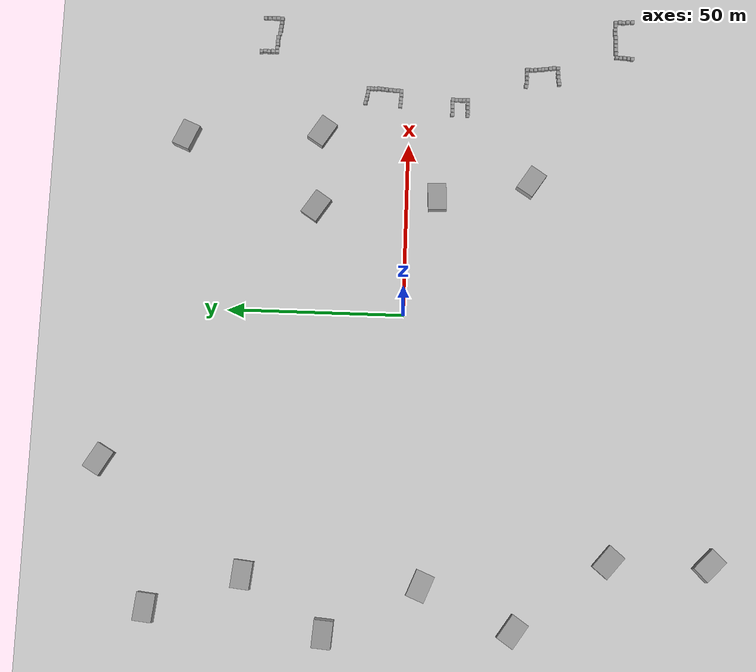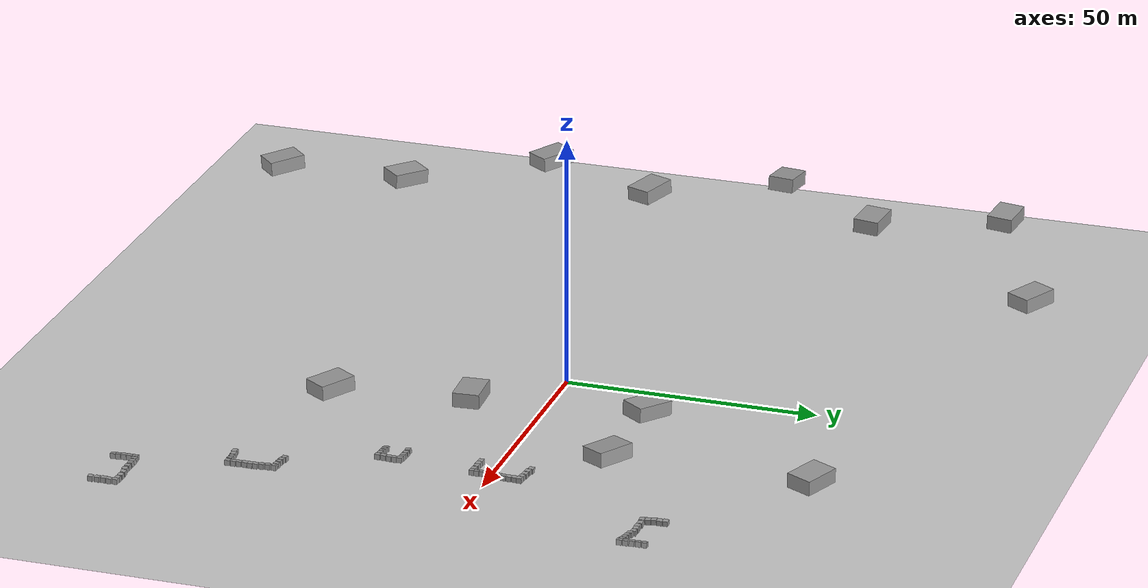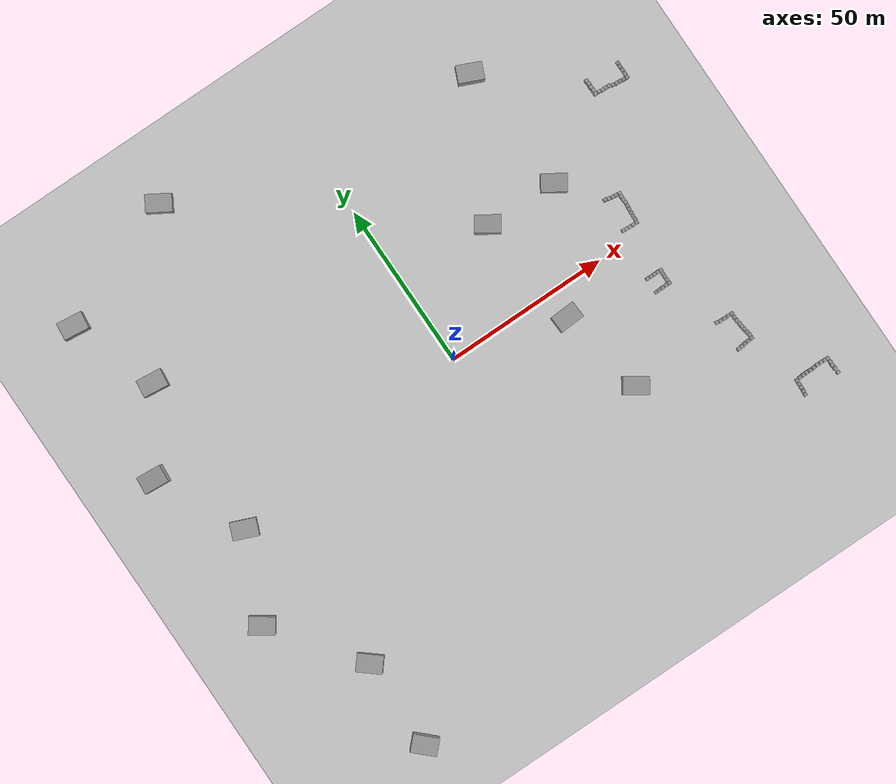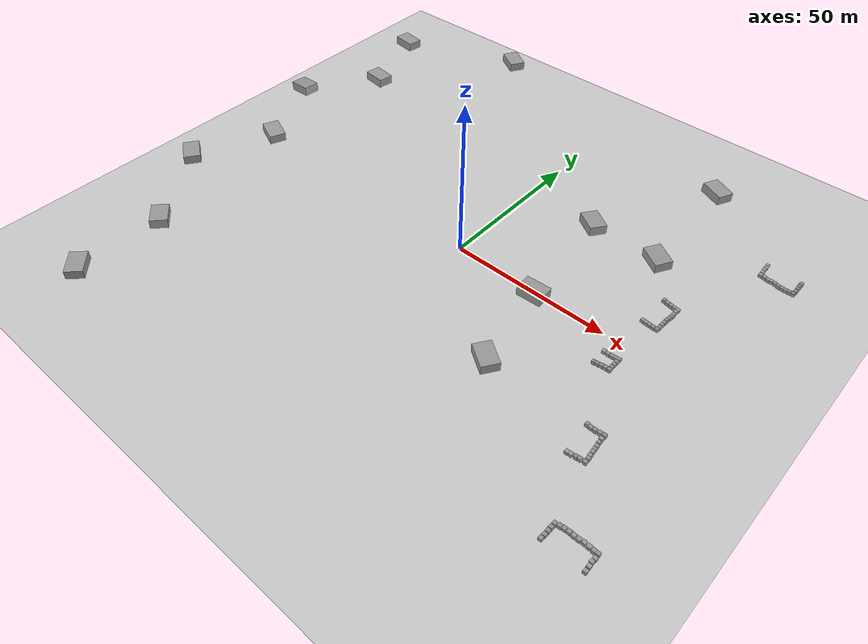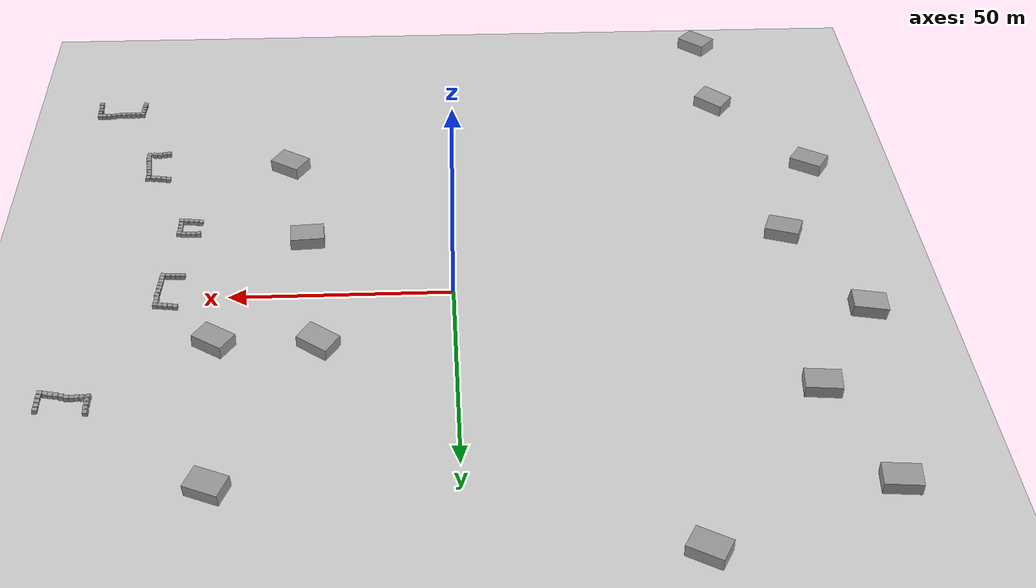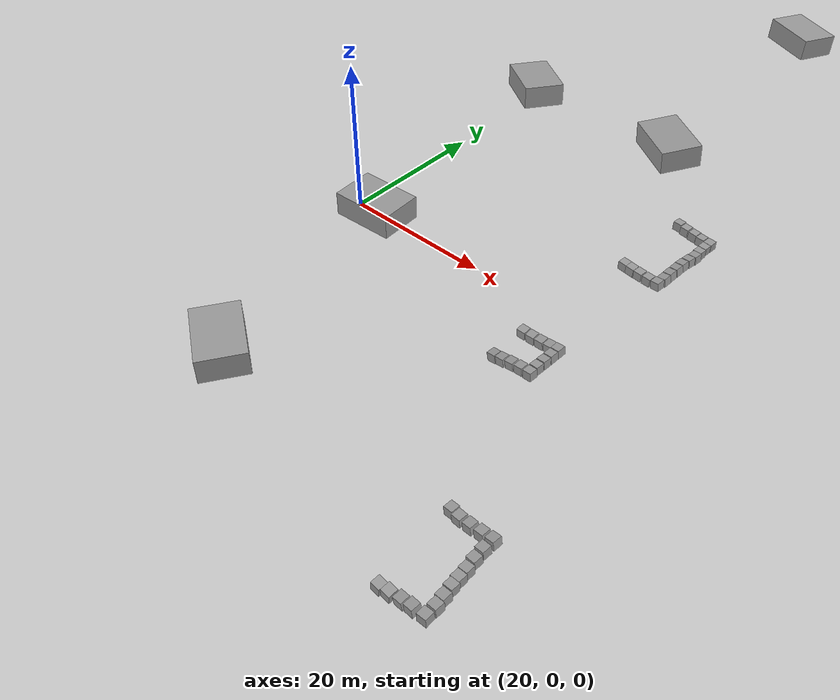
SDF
<sdf version="1.6">
 <world name="default">
  <light name="sun" type="directional">
   <pose>0 0 10 0 -0 0</pose>
   <diffuse>0.8 0.8 0.8 1</diffuse>
   <specular>0.2 0.2 0.2 1</specular>
   <attenuation>
    <range>1000</range>
    <constant>0.9</constant>
    <linear>0.01</linear>
    <quadratic>0.001</quadratic>
   </attenuation>
   <direction>-0.5 0.1 -0.9</direction>
  </light>
  <model name="ground_plane">
   <static>1</static>
   <link name="link">
    <collision name="collision">
     <geometry><plane><normal>0 0 1</normal><size>100 100</size></plane></geometry>
     <surface>
      <contact><collide_bitmask>65535</collide_bitmask></contact>
      <friction><ode><mu>100</mu><mu2>50</mu2></ode></friction>
     </surface>
    </collision>
    <visual name="visual">
     <cast_shadows>0</cast_shadows>
     <geometry><plane><normal>0 0 1</normal><size>100 100</size></plane></geometry>
     <material>
      <script><uri>model://media/materials/scripts/gazebo.material</uri><name>Gazebo/Grey</name></script>
     </material>
    </visual>
   </link>
  </model>
  <gravity>0 0 -9.8</gravity>
  <magnetic_field>6e-06 2.3e-05 -4.2e-05</magnetic_field>
  <atmosphere type="adiabatic"/>
  <physics name="default_physics" default="0" type="ode">
   <max_step_size>0.001</max_step_size>
   <real_time_factor>1</real_time_factor>
   <real_time_update_rate>1000</real_time_update_rate>
  </physics>
  <scene><ambient>0.4 0.4 0.4 1</ambient><background>0.7 0.7 0.7 1</background><shadows>1</shadows></scene>
  <spherical_coordinates>
   <surface_model>EARTH_WGS84</surface_model>
   <latitude_deg>0</latitude_deg>
   <longitude_deg>0</longitude_deg>
   <elevation>0</elevation>
   <heading_deg>0</heading_deg>
  </spherical_coordinates>
  <model name="unit_box">
   <pose>-43.2659 80.6704 10.9024 -0.008519 0.039988 -0.530913</pose>
   <link name="link">
    <inertial>
     <mass>1</mass>
     <inertia>
      <ixx>0.166667</ixx>
      <ixy>0</ixy>
      <ixz>0</ixz>
      <iyy>0.166667</iyy>
      <iyz>0</iyz>
      <izz>0.166667</izz>
     </inertia>
    </inertial>
    <collision name="collision"><geometry><box><size>7.46136 5.16116 2.86368</size></box></geometry></collision>
    <visual name="visual">
     <geometry><box><size>7.46136 5.16116 2.86368</size></box></geometry>
     <material>
      <script><name>Gazebo/Grey</name><uri>model://media/materials/scripts/gazebo.material</uri></script>
     </material>
    </visual>
   </link>
  </model>
  <model name="unit_box_clone">
   <pose>-72.4444 40.6455 10.5446 -0.027615 0.022279 -0.106732</pose>
   <link name="link">
    <inertial>
     <mass>1</mass>
     <inertia>
      <ixx>0.166667</ixx>
      <ixy>0</ixy>
      <ixz>0</ixz>
      <iyy>0.166667</iyy>
      <iyz>0</iyz>
      <izz>0.166667</izz>
     </inertia>
    </inertial>
    <collision name="collision"><geometry><box><size>7.46136 5.16116 2.86368</size></box></geometry></collision>
    <visual name="visual">
     <geometry><box><size>7.46136 5.16116 2.86368</size></box></geometry>
     <material>
      <script><name>Gazebo/Grey</name><uri>model://media/materials/scripts/gazebo.material</uri></script>
     </material>
    </visual>
   </link>
  </model>
  <model name="unit_box_clone_clone">
   <pose>-86.9891 18.5725 10.9854 -0.016932 -0.10172 -0.079737</pose>
   <link name="link">
    <inertial>
     <mass>1</mass>
     <inertia>
      <ixx>0.166667</ixx>
      <ixy>0</ixy>
      <ixz>0</ixz>
      <iyy>0.166667</iyy>
      <iyz>0</iyz>
      <izz>0.166667</izz>
     </inertia>
    </inertial>
    <collision name="collision"><geometry><box><size>7.46136 5.16116 2.86368</size></box></geometry></collision>
    <visual name="visual">
     <geometry><box><size>7.46136 5.16116 2.86368</size></box></geometry>
     <material>
      <script><name>Gazebo/Grey</name><uri>model://media/materials/scripts/gazebo.material</uri></script>
     </material>
    </visual>
   </link>
  </model>
  <model name="unit_box_clone_clone_clone_clone_0">
   <pose>-73.9835 -6.73196 10.7593 0.008439 0.066263 -0.390086</pose>
   <link name="link">
    <inertial>
     <mass>1</mass>
     <inertia>
      <ixx>0.166667</ixx>
      <ixy>0</ixy>
      <ixz>0</ixz>
      <iyy>0.166667</iyy>
      <iyz>0</iyz>
      <izz>0.166667</izz>
     </inertia>
    </inertial>
    <collision name="collision"><geometry><box><size>7.46136 5.16116 2.86368</size></box></geometry></collision>
    <visual name="visual">
     <geometry><box><size>7.46136 5.16116 2.86368</size></box></geometry>
     <material>
      <script><name>Gazebo/Grey</name><uri>model://media/materials/scripts/gazebo.material</uri></script>
     </material>
    </visual>
   </link>
  </model>
  <model name="unit_box_clone_clone_clone_clone_1">
   <pose>-66.1767 -56.6084 10.7654 -0.042448 -0.023895 -0.693496</pose>
   <link name="link">
    <inertial>
     <mass>1</mass>
     <inertia>
      <ixx>0.166667</ixx>
      <ixy>0</ixy>
      <ixz>0</ixz>
      <iyy>0.166667</iyy>
      <iyz>0</iyz>
      <izz>0.166667</izz>
     </inertia>
    </inertial>
    <collision name="collision"><geometry><box><size>7.46136 5.16116 2.86368</size></box></geometry></collision>
    <visual name="visual">
     <geometry><box><size>7.46136 5.16116 2.86368</size></box></geometry>
     <material>
      <script><name>Gazebo/Grey</name><uri>model://media/materials/scripts/gazebo.material</uri></script>
     </material>
    </visual>
   </link>
  </model>
  <model name="unit_box_clone_clone_clone_clone_2">
   <pose>-66.234 -83.5383 10.2936 0.000755 0.071402 -0.778903</pose>
   <link name="link">
    <inertial>
     <mass>1</mass>
     <inertia>
      <ixx>0.166667</ixx>
      <ixy>0</ixy>
      <ixz>0</ixz>
      <iyy>0.166667</iyy>
      <iyz>0</iyz>
      <izz>0.166667</izz>
     </inertia>
    </inertial>
    <collision name="collision"><geometry><box><size>7.46136 5.16116 2.86368</size></box></geometry></collision>
    <visual name="visual">
     <geometry><box><size>7.46136 5.16116 2.86368</size></box></geometry>
     <material>
      <script><name>Gazebo/Grey</name><uri>model://media/materials/scripts/gazebo.material</uri></script>
     </material>
    </visual>
   </link>
  </model>
  <model name="unit_box_clone_clone_clone_clone_3">
   <pose>32.1348 -8.34286 10.2487 0.006799 0.009123 0.052458</pose>
   <link name="link">
    <inertial>
     <mass>1</mass>
     <inertia>
      <ixx>0.166667</ixx>
      <ixy>0</ixy>
      <ixz>0</ixz>
      <iyy>0.166667</iyy>
      <iyz>0</iyz>
      <izz>0.166667</izz>
     </inertia>
    </inertial>
    <collision name="collision"><geometry><box><size>7.46136 5.16116 2.86368</size></box></geometry></collision>
    <visual name="visual">
     <geometry><box><size>7.46136 5.16116 2.86368</size></box></geometry>
     <material>
      <script><name>Gazebo/Grey</name><uri>model://media/materials/scripts/gazebo.material</uri></script>
     </material>
    </visual>
   </link>
  </model>
  <model name="unit_box_clone_clone_clone_clone_4">
   <pose>28.4662 25.1159 10.4371 -0.019179 -0.048489 -0.59442</pose>
   <link name="link">
    <inertial>
     <mass>1</mass>
     <inertia>
      <ixx>0.166667</ixx>
      <ixy>0</ixy>
      <ixz>0</ixz>
      <iyy>0.166667</iyy>
      <iyz>0</iyz>
      <izz>0.166667</izz>
     </inertia>
    </inertial>
    <collision name="collision"><geometry><box><size>7.46136 5.16116 2.86368</size></box></geometry></collision>
    <visual name="visual">
     <geometry><box><size>7.46136 5.16116 2.86368</size></box></geometry>
     <material>
      <script><name>Gazebo/Grey</name><uri>model://media/materials/scripts/gazebo.material</uri></script>
     </material>
    </visual>
   </link>
  </model>
  <model name="unit_box_0">
   <pose>56.8082 -12.0348 8.51934 0.068702 0.024979 0.001606</pose>
   <link name="link">
    <inertial>
     <mass>1</mass>
     <inertia>
      <ixx>0.166667</ixx>
      <ixy>0</ixy>
      <ixz>0</ixz>
      <iyy>0.166667</iyy>
      <iyz>0</iyz>
      <izz>0.166667</izz>
     </inertia>
    </inertial>
    <collision name="collision"><geometry><box><size>1 1 1</size></box></geometry></collision>
    <visual name="visual">
     <geometry><box><size>1 1 1</size></box></geometry>
     <material>
      <script><name>Gazebo/Grey</name><uri>model://media/materials/scripts/gazebo.material</uri></script>
     </material>
    </visual>
   </link>
  </model>
  <model name="unit_box_0_clone">
   <pose>57.9458 -12.0443 8.51511 0.070283 -0.023568 -0.001616</pose>
   <link name="link">
    <inertial>
     <mass>1</mass>
     <inertia>
      <ixx>0.166667</ixx>
      <ixy>0</ixy>
      <ixz>0</ixz>
      <iyy>0.166667</iyy>
      <iyz>0</iyz>
      <izz>0.166667</izz>
     </inertia>
    </inertial>
    <collision name="collision"><geometry><box><size>1 1 1</size></box></geometry></collision>
    <visual name="visual">
     <geometry><box><size>1 1 1</size></box></geometry>
     <material>
      <script><name>Gazebo/Grey</name><uri>model://media/materials/scripts/gazebo.material</uri></script>
     </material>
    </visual>
   </link>
  </model>
  <model name="unit_box_0_clone_clone">
   <pose>59.0801 -12.0425 8.55387 0.065589 -0.044973 -0.014319</pose>
   <link name="link">
    <inertial>
     <mass>1</mass>
     <inertia>
      <ixx>0.166667</ixx>
      <ixy>0</ixy>
      <ixz>0</ixz>
      <iyy>0.166667</iyy>
      <iyz>0</iyz>
      <izz>0.166667</izz>
     </inertia>
    </inertial>
    <collision name="collision"><geometry><box><size>1 1 1</size></box></geometry></collision>
    <visual name="visual">
     <geometry><box><size>1 1 1</size></box></geometry>
     <material>
      <script><name>Gazebo/Grey</name><uri>model://media/materials/scripts/gazebo.material</uri></script>
     </material>
    </visual>
   </link>
  </model>
  <model name="unit_box_0_clone_clone_0">
   <pose>60.1729 -12.0171 8.6179 0.071993 -0.068565 -0.027561</pose>
   <link name="link">
    <inertial>
     <mass>1</mass>
     <inertia>
      <ixx>0.166667</ixx>
      <ixy>0</ixy>
      <ixz>0</ixz>
      <iyy>0.166667</iyy>
      <iyz>0</iyz>
      <izz>0.166667</izz>
     </inertia>
    </inertial>
    <collision name="collision"><geometry><box><size>1 1 1</size></box></geometry></collision>
    <visual name="visual">
     <geometry><box><size>1 1 1</size></box></geometry>
     <material>
      <script><name>Gazebo/Grey</name><uri>model://media/materials/scripts/gazebo.material</uri></script>
     </material>
    </visual>
   </link>
  </model>
  <model name="unit_box_0_clone_clone_1">
   <pose>61.164 -12.0739 8.76441 0.013393 -0.068581 -0.027556</pose>
   <link name="link">
    <inertial>
     <mass>1</mass>
     <inertia>
      <ixx>0.166667</ixx>
      <ixy>0</ixy>
      <ixz>0</ixz>
      <iyy>0.166667</iyy>
      <iyz>0</iyz>
      <izz>0.166667</izz>
     </inertia>
    </inertial>
    <collision name="collision"><geometry><box><size>1 1 1</size></box></geometry></collision>
    <visual name="visual">
     <geometry><box><size>1 1 1</size></box></geometry>
     <material>
      <script><name>Gazebo/Grey</name><uri>model://media/materials/scripts/gazebo.material</uri></script>
     </material>
    </visual>
   </link>
  </model>
  <model name="unit_box_0_clone_clone_2">
   <pose>61.075 -13.0706 8.66073 0.013406 -0.081049 -0.027722</pose>
   <link name="link">
    <inertial>
     <mass>1</mass>
     <inertia>
      <ixx>0.166667</ixx>
      <ixy>0</ixy>
      <ixz>0</ixz>
      <iyy>0.166667</iyy>
      <iyz>0</iyz>
      <izz>0.166667</izz>
     </inertia>
    </inertial>
    <collision name="collision"><geometry><box><size>1 1 1</size></box></geometry></collision>
    <visual name="visual">
     <geometry><box><size>1 1 1</size></box></geometry>
     <material>
      <script><name>Gazebo/Grey</name><uri>model://media/materials/scripts/gazebo.material</uri></script>
     </material>
    </visual>
   </link>
  </model>
  <model name="unit_box_0_clone_clone_3">
   <pose>61.058 -14.1773 8.68275 -0.052948 -0.073073 -0.032754</pose>
   <link name="link">
    <inertial>
     <mass>1</mass>
     <inertia>
      <ixx>0.166667</ixx>
      <ixy>0</ixy>
      <ixz>0</ixz>
      <iyy>0.166667</iyy>
      <iyz>0</iyz>
      <izz>0.166667</izz>
     </inertia>
    </inertial>
    <collision name="collision"><geometry><box><size>1 1 1</size></box></geometry></collision>
    <visual name="visual">
     <geometry><box><size>1 1 1</size></box></geometry>
     <material>
      <script><name>Gazebo/Grey</name><uri>model://media/materials/scripts/gazebo.material</uri></script>
     </material>
    </visual>
   </link>
  </model>
  <model name="unit_box_0_clone_clone_4">
   <pose>61.0389 -15.2718 8.72611 -0.047844 -0.047895 -0.043761</pose>
   <link name="link">
    <inertial>
     <mass>1</mass>
     <inertia>
      <ixx>0.166667</ixx>
      <ixy>0</ixy>
      <ixz>0</ixz>
      <iyy>0.166667</iyy>
      <iyz>0</iyz>
      <izz>0.166667</izz>
     </inertia>
    </inertial>
    <collision name="collision"><geometry><box><size>1 1 1</size></box></geometry></collision>
    <visual name="visual">
     <geometry><box><size>1 1 1</size></box></geometry>
     <material>
      <script><name>Gazebo/Grey</name><uri>model://media/materials/scripts/gazebo.material</uri></script>
     </material>
    </visual>
   </link>
  </model>
  <model name="unit_box_0_clone_clone_5">
   <pose>61.0917 -16.3753 8.78077 -0.033775 -0.068538 -0.037248</pose>
   <link name="link">
    <inertial>
     <mass>1</mass>
     <inertia>
      <ixx>0.166667</ixx>
      <ixy>0</ixy>
      <ixz>0</ixz>
      <iyy>0.166667</iyy>
      <iyz>0</iyz>
      <izz>0.166667</izz>
     </inertia>
    </inertial>
    <collision name="collision"><geometry><box><size>1 1 1</size></box></geometry></collision>
    <visual name="visual">
     <geometry><box><size>1 1 1</size></box></geometry>
     <material>
      <script><name>Gazebo/Grey</name><uri>model://media/materials/scripts/gazebo.material</uri></script>
     </material>
    </visual>
   </link>
  </model>
  <model name="unit_box_0_clone_clone_5_clone">
   <pose>59.984 -16.3311 8.72264 0.021232 -0.077955 -0.041553</pose>
   <link name="link">
    <inertial>
     <mass>1</mass>
     <inertia>
      <ixx>0.166667</ixx>
      <ixy>0</ixy>
      <ixz>0</ixz>
      <iyy>0.166667</iyy>
      <iyz>0</iyz>
      <izz>0.166667</izz>
     </inertia>
    </inertial>
    <collision name="collision"><geometry><box><size>1 1 1</size></box></geometry></collision>
    <visual name="visual">
     <geometry><box><size>1 1 1</size></box></geometry>
     <material>
      <script><name>Gazebo/Grey</name><uri>model://media/materials/scripts/gazebo.material</uri></script>
     </material>
    </visual>
   </link>
  </model>
  <model name="unit_box_0_clone_clone_5_clone_0">
   <pose>58.8619 -16.3381 8.61438 0.043035 -0.140372 -0.027138</pose>
   <link name="link">
    <inertial>
     <mass>1</mass>
     <inertia>
      <ixx>0.166667</ixx>
      <ixy>0</ixy>
      <ixz>0</ixz>
      <iyy>0.166667</iyy>
      <iyz>0</iyz>
      <izz>0.166667</izz>
     </inertia>
    </inertial>
    <collision name="collision"><geometry><box><size>1 1 1</size></box></geometry></collision>
    <visual name="visual">
     <geometry><box><size>1 1 1</size></box></geometry>
     <material>
      <script><name>Gazebo/Grey</name><uri>model://media/materials/scripts/gazebo.material</uri></script>
     </material>
    </visual>
   </link>
  </model>
  <model name="unit_box_0_clone_clone_5_clone_1">
   <pose>57.7313 -16.3962 8.45456 0.039115 -0.140751 -0.046621</pose>
   <link name="link">
    <inertial>
     <mass>1</mass>
     <inertia>
      <ixx>0.166667</ixx>
      <ixy>0</ixy>
      <ixz>0</ixz>
      <iyy>0.166667</iyy>
      <iyz>0</iyz>
      <izz>0.166667</izz>
     </inertia>
    </inertial>
    <collision name="collision"><geometry><box><size>1 1 1</size></box></geometry></collision>
    <visual name="visual">
     <geometry><box><size>1 1 1</size></box></geometry>
     <material>
      <script><name>Gazebo/Grey</name><uri>model://media/materials/scripts/gazebo.material</uri></script>
     </material>
    </visual>
   </link>
  </model>
  <model name="unit_box_0_clone_clone_5_clone_2">
   <pose>56.687 -16.4022 8.30608 0.009797 -0.166075 -0.056845</pose>
   <link name="link">
    <inertial>
     <mass>1</mass>
     <inertia>
      <ixx>0.166667</ixx>
      <ixy>0</ixy>
      <ixz>0</ixz>
      <iyy>0.166667</iyy>
      <iyz>0</iyz>
      <izz>0.166667</izz>
     </inertia>
    </inertial>
    <collision name="collision"><geometry><box><size>1 1 1</size></box></geometry></collision>
    <visual name="visual">
     <geometry><box><size>1 1 1</size></box></geometry>
     <material>
      <script><name>Gazebo/Grey</name><uri>model://media/materials/scripts/gazebo.material</uri></script>
     </material>
    </visual>
   </link>
  </model>
  <model name="unit_box_clone_clone_clone_clone_4_clone">
   <pose>47.8588 62.4687 9.94634 -0.04945 0.022573 -0.408771</pose>
   <link name="link">
    <inertial>
     <mass>1</mass>
     <inertia>
      <ixx>0.166667</ixx>
      <ixy>0</ixy>
      <ixz>0</ixz>
      <iyy>0.166667</iyy>
      <iyz>0</iyz>
      <izz>0.166667</izz>
     </inertia>
    </inertial>
    <collision name="collision"><geometry><box><size>7.46136 5.16116 2.86368</size></box></geometry></collision>
    <visual name="visual">
     <geometry><box><size>7.46136 5.16116 2.86368</size></box></geometry>
     <material>
      <script><name>Gazebo/Grey</name><uri>model://media/materials/scripts/gazebo.material</uri></script>
     </material>
    </visual>
   </link>
  </model>
  <model name="unit_box_clone_clone_clone_clone_4_clone_0">
   <pose>49.9442 24.3203 10.6228 0.054548 0.000494 -0.570507</pose>
   <link name="link">
    <inertial>
     <mass>1</mass>
     <inertia>
      <ixx>0.166667</ixx>
      <ixy>0</ixy>
      <ixz>0</ixz>
      <iyy>0.166667</iyy>
      <iyz>0</iyz>
      <izz>0.166667</izz>
     </inertia>
    </inertial>
    <collision name="collision"><geometry><box><size>7.46136 5.16116 2.86368</size></box></geometry></collision>
    <visual name="visual">
     <geometry><box><size>7.46136 5.16116 2.86368</size></box></geometry>
     <material>
      <script><name>Gazebo/Grey</name><uri>model://media/materials/scripts/gazebo.material</uri></script>
     </material>
    </visual>
   </link>
  </model>
  <model name="unit_box_clone_clone_clone_clone_4_clone_1">
   <pose>37.1729 -34.505 10.6142 0.007164 0.034748 -0.582037</pose>
   <link name="link">
    <inertial>
     <mass>1</mass>
     <inertia>
      <ixx>0.166667</ixx>
      <ixy>0</ixy>
      <ixz>0</ixz>
      <iyy>0.166667</iyy>
      <iyz>0</iyz>
      <izz>0.166667</izz>
     </inertia>
    </inertial>
    <collision name="collision"><geometry><box><size>7.46136 5.16116 2.86368</size></box></geometry></collision>
    <visual name="visual">
     <geometry><box><size>7.46136 5.16116 2.86368</size></box></geometry>
     <material>
      <script><name>Gazebo/Grey</name><uri>model://media/materials/scripts/gazebo.material</uri></script>
     </material>
    </visual>
   </link>
  </model>
  <model name="unit_box_0_clone_clone_5_clone_2_clone">
   <pose>65.9663 -32.8177 8.0495 -0.009677 -0.063341 -0.051419</pose>
   <link name="link">
    <inertial>
     <mass>1</mass>
     <inertia>
      <ixx>0.166667</ixx>
      <ixy>0</ixy>
      <ixz>0</ixz>
      <iyy>0.166667</iyy>
      <iyz>0</iyz>
      <izz>0.166667</izz>
     </inertia>
    </inertial>
    <collision name="collision"><geometry><box><size>1 1 1</size></box></geometry></collision>
    <visual name="visual">
     <geometry><box><size>1 1 1</size></box></geometry>
     <material>
      <script><name>Gazebo/Grey</name><uri>model://media/materials/scripts/gazebo.material</uri></script>
     </material>
    </visual>
   </link>
  </model>
  <model name="unit_box_0_clone_clone_5_clone_2_clone_0">
   <pose>67.0313 -33.0162 8.09398 0.024812 -0.048671 -0.073486</pose>
   <link name="link">
    <inertial>
     <mass>1</mass>
     <inertia>
      <ixx>0.166667</ixx>
      <ixy>0</ixy>
      <ixz>0</ixz>
      <iyy>0.166667</iyy>
      <iyz>0</iyz>
      <izz>0.166667</izz>
     </inertia>
    </inertial>
    <collision name="collision"><geometry><box><size>1 1 1</size></box></geometry></collision>
    <visual name="visual">
     <geometry><box><size>1 1 1</size></box></geometry>
     <material>
      <script><name>Gazebo/Grey</name><uri>model://media/materials/scripts/gazebo.material</uri></script>
     </material>
    </visual>
   </link>
  </model>
  <model name="unit_box_0_clone_clone_5_clone_2_clone_1">
   <pose>68.288 -33.0633 8.19772 0.01308 -0.108704 -0.072441</pose>
   <link name="link">
    <inertial>
     <mass>1</mass>
     <inertia>
      <ixx>0.166667</ixx>
      <ixy>0</ixy>
      <ixz>0</ixz>
      <iyy>0.166667</iyy>
      <iyz>0</iyz>
      <izz>0.166667</izz>
     </inertia>
    </inertial>
    <collision name="collision"><geometry><box><size>1 1 1</size></box></geometry></collision>
    <visual name="visual">
     <geometry><box><size>1 1 1</size></box></geometry>
     <material>
      <script><name>Gazebo/Grey</name><uri>model://media/materials/scripts/gazebo.material</uri></script>
     </material>
    </visual>
   </link>
  </model>
  <model name="unit_box_0_clone_clone_5_clone_2_clone_2">
   <pose>69.5357 -33.0297 8.28716 -0.029392 -0.081009 -0.047046</pose>
   <link name="link">
    <inertial>
     <mass>1</mass>
     <inertia>
      <ixx>0.166667</ixx>
      <ixy>0</ixy>
      <ixz>0</ixz>
      <iyy>0.166667</iyy>
      <iyz>0</iyz>
      <izz>0.166667</izz>
     </inertia>
    </inertial>
    <collision name="collision"><geometry><box><size>1 1 1</size></box></geometry></collision>
    <visual name="visual">
     <geometry><box><size>1 1 1</size></box></geometry>
     <material>
      <script><name>Gazebo/Grey</name><uri>model://media/materials/scripts/gazebo.material</uri></script>
     </material>
    </visual>
   </link>
  </model>
  <model name="unit_box_0_clone_clone_5_clone_2_clone_3">
   <pose>70.7545 -33.0122 8.4023 -0.009359 -0.139514 -0.059721</pose>
   <link name="link">
    <inertial>
     <mass>1</mass>
     <inertia>
      <ixx>0.166667</ixx>
      <ixy>0</ixy>
      <ixz>0</ixz>
      <iyy>0.166667</iyy>
      <iyz>0</iyz>
      <izz>0.166667</izz>
     </inertia>
    </inertial>
    <collision name="collision"><geometry><box><size>1 1 1</size></box></geometry></collision>
    <visual name="visual">
     <geometry><box><size>1 1 1</size></box></geometry>
     <material>
      <script><name>Gazebo/Grey</name><uri>model://media/materials/scripts/gazebo.material</uri></script>
     </material>
    </visual>
   </link>
  </model>
  <model name="unit_box_0_clone_clone_5_clone_2_clone_4">
   <pose>70.712 -34.2452 8.37365 0.012474 -0.079712 -0.05874</pose>
   <link name="link">
    <inertial>
     <mass>1</mass>
     <inertia>
      <ixx>0.166667</ixx>
      <ixy>0</ixy>
      <ixz>0</ixz>
      <iyy>0.166667</iyy>
      <iyz>0</iyz>
      <izz>0.166667</izz>
     </inertia>
    </inertial>
    <collision name="collision"><geometry><box><size>1 1 1</size></box></geometry></collision>
    <visual name="visual">
     <geometry><box><size>1 1 1</size></box></geometry>
     <material>
      <script><name>Gazebo/Grey</name><uri>model://media/materials/scripts/gazebo.material</uri></script>
     </material>
    </visual>
   </link>
  </model>
  <model name="unit_box_0_clone_clone_5_clone_2_clone_5">
   <pose>70.7845 -35.4094 8.34165 0.028852 -0.049301 -0.061353</pose>
   <link name="link">
    <inertial>
     <mass>1</mass>
     <inertia>
      <ixx>0.166667</ixx>
      <ixy>0</ixy>
      <ixz>0</ixz>
      <iyy>0.166667</iyy>
      <iyz>0</iyz>
      <izz>0.166667</izz>
     </inertia>
    </inertial>
    <collision name="collision"><geometry><box><size>1 1 1</size></box></geometry></collision>
    <visual name="visual">
     <geometry><box><size>1 1 1</size></box></geometry>
     <material>
      <script><name>Gazebo/Grey</name><uri>model://media/materials/scripts/gazebo.material</uri></script>
     </material>
    </visual>
   </link>
  </model>
  <model name="unit_box_0_clone_clone_5_clone_2_clone_6">
   <pose>70.9628 -36.5823 8.36307 -0.054994 -0.047926 -0.009928</pose>
   <link name="link">
    <inertial>
     <mass>1</mass>
     <inertia>
      <ixx>0.166667</ixx>
      <ixy>0</ixy>
      <ixz>0</ixz>
      <iyy>0.166667</iyy>
      <iyz>0</iyz>
      <izz>0.166667</izz>
     </inertia>
    </inertial>
    <collision name="collision"><geometry><box><size>1 1 1</size></box></geometry></collision>
    <visual name="visual">
     <geometry><box><size>1 1 1</size></box></geometry>
     <material>
      <script><name>Gazebo/Grey</name><uri>model://media/materials/scripts/gazebo.material</uri></script>
     </material>
    </visual>
   </link>
  </model>
  <model name="unit_box_0_clone_clone_5_clone_2_clone_7">
   <pose>71.022 -37.585 8.35634 -0.054984 -0.029039 -0.010978</pose>
   <link name="link">
    <inertial>
     <mass>1</mass>
     <inertia>
      <ixx>0.166667</ixx>
      <ixy>0</ixy>
      <ixz>0</ixz>
      <iyy>0.166667</iyy>
      <iyz>0</iyz>
      <izz>0.166667</izz>
     </inertia>
    </inertial>
    <collision name="collision"><geometry><box><size>1 1 1</size></box></geometry></collision>
    <visual name="visual">
     <geometry><box><size>1 1 1</size></box></geometry>
     <material>
      <script><name>Gazebo/Grey</name><uri>model://media/materials/scripts/gazebo.material</uri></script>
     </material>
    </visual>
   </link>
  </model>
  <model name="unit_box_0_clone_clone_5_clone_2_clone_8">
   <pose>71.1512 -38.5954 8.43974 -0.079454 -0.026746 -0.011143</pose>
   <link name="link">
    <inertial>
     <mass>1</mass>
     <inertia>
      <ixx>0.166667</ixx>
      <ixy>0</ixy>
      <ixz>0</ixz>
      <iyy>0.166667</iyy>
      <iyz>0</iyz>
      <izz>0.166667</izz>
     </inertia>
    </inertial>
    <collision name="collision"><geometry><box><size>1 1 1</size></box></geometry></collision>
    <visual name="visual">
     <geometry><box><size>1 1 1</size></box></geometry>
     <material>
      <script><name>Gazebo/Grey</name><uri>model://media/materials/scripts/gazebo.material</uri></script>
     </material>
    </visual>
   </link>
  </model>
  <model name="unit_box_0_clone_clone_5_clone_2_clone_9">
   <pose>71.3168 -39.6518 8.4976 0.012194 -0.06355 -0.033442</pose>
   <link name="link">
    <inertial>
     <mass>1</mass>
     <inertia>
      <ixx>0.166667</ixx>
      <ixy>0</ixy>
      <ixz>0</ixz>
      <iyy>0.166667</iyy>
      <iyz>0</iyz>
      <izz>0.166667</izz>
     </inertia>
    </inertial>
    <collision name="collision"><geometry><box><size>1 1 1</size></box></geometry></collision>
    <visual name="visual">
     <geometry><box><size>1 1 1</size></box></geometry>
     <material>
      <script><name>Gazebo/Grey</name><uri>model://media/materials/scripts/gazebo.material</uri></script>
     </material>
    </visual>
   </link>
  </model>
  <model name="unit_box_0_clone_clone_5_clone_2_clone_10">
   <pose>71.4637 -40.6971 8.51288 -0.008278 -0.070346 -0.039338</pose>
   <link name="link">
    <inertial>
     <mass>1</mass>
     <inertia>
      <ixx>0.166667</ixx>
      <ixy>0</ixy>
      <ixz>0</ixz>
      <iyy>0.166667</iyy>
      <iyz>0</iyz>
      <izz>0.166667</izz>
     </inertia>
    </inertial>
    <collision name="collision"><geometry><box><size>1 1 1</size></box></geometry></collision>
    <visual name="visual">
     <geometry><box><size>1 1 1</size></box></geometry>
     <material>
      <script><name>Gazebo/Grey</name><uri>model://media/materials/scripts/gazebo.material</uri></script>
     </material>
    </visual>
   </link>
  </model>
  <model name="unit_box_0_clone_clone_5_clone_2_clone_11">
   <pose>71.4317 -41.8346 8.50306 0.005621 -0.045023 0.012802</pose>
   <link name="link">
    <inertial>
     <mass>1</mass>
     <inertia>
      <ixx>0.166667</ixx>
      <ixy>0</ixy>
      <ixz>0</ixz>
      <iyy>0.166667</iyy>
      <iyz>0</iyz>
      <izz>0.166667</izz>
     </inertia>
    </inertial>
    <collision name="collision"><geometry><box><size>1 1 1</size></box></geometry></collision>
    <visual name="visual">
     <geometry><box><size>1 1 1</size></box></geometry>
     <material>
      <script><name>Gazebo/Grey</name><uri>model://media/materials/scripts/gazebo.material</uri></script>
     </material>
    </visual>
   </link>
  </model>
  <model name="unit_box_0_clone_clone_5_clone_2_clone_12">
   <pose>70.1063 -41.907 8.42726 0.030607 -0.097137 -0.077572</pose>
   <link name="link">
    <inertial>
     <mass>1</mass>
     <inertia>
      <ixx>0.166667</ixx>
      <ixy>0</ixy>
      <ixz>0</ixz>
      <iyy>0.166667</iyy>
      <iyz>0</iyz>
      <izz>0.166667</izz>
     </inertia>
    </inertial>
    <collision name="collision"><geometry><box><size>1 1 1</size></box></geometry></collision>
    <visual name="visual">
     <geometry><box><size>1 1 1</size></box></geometry>
     <material>
      <script><name>Gazebo/Grey</name><uri>model://media/materials/scripts/gazebo.material</uri></script>
     </material>
    </visual>
   </link>
  </model>
  <model name="unit_box_0_clone_clone_5_clone_2_clone_13">
   <pose>69.0108 -41.9505 8.32343 0.075912 -0.107909 -0.064497</pose>
   <link name="link">
    <inertial>
     <mass>1</mass>
     <inertia>
      <ixx>0.166667</ixx>
      <ixy>0</ixy>
      <ixz>0</ixz>
      <iyy>0.166667</iyy>
      <iyz>0</iyz>
      <izz>0.166667</izz>
     </inertia>
    </inertial>
    <collision name="collision"><geometry><box><size>1 1 1</size></box></geometry></collision>
    <visual name="visual">
     <geometry><box><size>1 1 1</size></box></geometry>
     <material>
      <script><name>Gazebo/Grey</name><uri>model://media/materials/scripts/gazebo.material</uri></script>
     </material>
    </visual>
   </link>
  </model>
  <model name="unit_box_0_clone_clone_5_clone_2_clone_14">
   <pose>67.8035 -42.1425 8.32225 0.054719 0.089637 -0.036269</pose>
   <link name="link">
    <inertial>
     <mass>1</mass>
     <inertia>
      <ixx>0.166667</ixx>
      <ixy>0</ixy>
      <ixz>0</ixz>
      <iyy>0.166667</iyy>
      <iyz>0</iyz>
      <izz>0.166667</izz>
     </inertia>
    </inertial>
    <collision name="collision"><geometry><box><size>1 1 1</size></box></geometry></collision>
    <visual name="visual">
     <geometry><box><size>1 1 1</size></box></geometry>
     <material>
      <script><name>Gazebo/Grey</name><uri>model://media/materials/scripts/gazebo.material</uri></script>
     </material>
    </visual>
   </link>
  </model>
  <model name="unit_box_0_clone_clone_5_clone_2_clone_15">
   <pose>66.801 -42.2758 8.40059 0.009057 0.089644 -0.036269</pose>
   <link name="link">
    <inertial>
     <mass>1</mass>
     <inertia>
      <ixx>0.166667</ixx>
      <ixy>0</ixy>
      <ixz>0</ixz>
      <iyy>0.166667</iyy>
      <iyz>0</iyz>
      <izz>0.166667</izz>
     </inertia>
    </inertial>
    <collision name="collision"><geometry><box><size>1 1 1</size></box></geometry></collision>
    <visual name="visual">
     <geometry><box><size>1 1 1</size></box></geometry>
     <material>
      <script><name>Gazebo/Grey</name><uri>model://media/materials/scripts/gazebo.material</uri></script>
     </material>
    </visual>
   </link>
  </model>
  <model name="unit_box_0_clone_clone_5_clone_2_clone_16">
   <pose>63.5557 8.88397 9.21975 -0.024053 -0.074124 -0.070389</pose>
   <link name="link">
    <inertial>
     <mass>1</mass>
     <inertia>
      <ixx>0.166667</ixx>
      <ixy>0</ixy>
      <ixz>0</ixz>
      <iyy>0.166667</iyy>
      <iyz>0</iyz>
      <izz>0.166667</izz>
     </inertia>
    </inertial>
    <collision name="collision"><geometry><box><size>1 1 1</size></box></geometry></collision>
    <visual name="visual">
     <geometry><box><size>1 1 1</size></box></geometry>
     <material>
      <script><name>Gazebo/Grey</name><uri>model://media/materials/scripts/gazebo.material</uri></script>
     </material>
    </visual>
   </link>
  </model>
  <model name="unit_box_0_clone_clone_5_clone_2_clone_16_clone">
   <pose>63.4192 7.82116 9.26519 -0.04298 -0.095834 -0.073607</pose>
   <link name="link">
    <inertial>
     <mass>1</mass>
     <inertia>
      <ixx>0.166667</ixx>
      <ixy>0</ixy>
      <ixz>0</ixz>
      <iyy>0.166667</iyy>
      <iyz>0</iyz>
      <izz>0.166667</izz>
     </inertia>
    </inertial>
    <collision name="collision"><geometry><box><size>1 1 1</size></box></geometry></collision>
    <visual name="visual">
     <geometry><box><size>1 1 1</size></box></geometry>
     <material>
      <script><name>Gazebo/Grey</name><uri>model://media/materials/scripts/gazebo.material</uri></script>
     </material>
    </visual>
   </link>
  </model>
  <model name="unit_box_0_clone_clone_5_clone_2_clone_16_clone_0">
   <pose>63.3074 6.74529 9.30209 -0.009325 -0.121154 -0.067689</pose>
   <link name="link">
    <inertial>
     <mass>1</mass>
     <inertia>
      <ixx>0.166667</ixx>
      <ixy>0</ixy>
      <ixz>0</ixz>
      <iyy>0.166667</iyy>
      <iyz>0</iyz>
      <izz>0.166667</izz>
     </inertia>
    </inertial>
    <collision name="collision"><geometry><box><size>1 1 1</size></box></geometry></collision>
    <visual name="visual">
     <geometry><box><size>1 1 1</size></box></geometry>
     <material>
      <script><name>Gazebo/Grey</name><uri>model://media/materials/scripts/gazebo.material</uri></script>
     </material>
    </visual>
   </link>
  </model>
  <model name="unit_box_0_clone_clone_5_clone_2_clone_16_clone_1">
   <pose>63.2538 5.70484 9.28665 0.055892 -0.135657 -0.091232</pose>
   <link name="link">
    <inertial>
     <mass>1</mass>
     <inertia>
      <ixx>0.166667</ixx>
      <ixy>0</ixy>
      <ixz>0</ixz>
      <iyy>0.166667</iyy>
      <iyz>0</iyz>
      <izz>0.166667</izz>
     </inertia>
    </inertial>
    <collision name="collision"><geometry><box><size>1 1 1</size></box></geometry></collision>
    <visual name="visual">
     <geometry><box><size>1 1 1</size></box></geometry>
     <material>
      <script><name>Gazebo/Grey</name><uri>model://media/materials/scripts/gazebo.material</uri></script>
     </material>
    </visual>
   </link>
  </model>
  <model name="unit_box_0_clone_clone_5_clone_2_clone_16_clone_2">
   <pose>63.1738 4.62657 9.23314 0.043713 -0.13876 -0.069372</pose>
   <link name="link">
    <inertial>
     <mass>1</mass>
     <inertia>
      <ixx>0.166667</ixx>
      <ixy>0</ixy>
      <ixz>0</ixz>
      <iyy>0.166667</iyy>
      <iyz>0</iyz>
      <izz>0.166667</izz>
     </inertia>
    </inertial>
    <collision name="collision"><geometry><box><size>1 1 1</size></box></geometry></collision>
    <visual name="visual">
     <geometry><box><size>1 1 1</size></box></geometry>
     <material>
      <script><name>Gazebo/Grey</name><uri>model://media/materials/scripts/gazebo.material</uri></script>
     </material>
    </visual>
   </link>
  </model>
  <model name="unit_box_0_clone_clone_5_clone_2_clone_16_clone_3">
   <pose>63.1374 3.5606 9.19277 0.038659 -0.13594 -0.069385</pose>
   <link name="link">
    <inertial>
     <mass>1</mass>
     <inertia>
      <ixx>0.166667</ixx>
      <ixy>0</ixy>
      <ixz>0</ixz>
      <iyy>0.166667</iyy>
      <iyz>0</iyz>
      <izz>0.166667</izz>
     </inertia>
    </inertial>
    <collision name="collision"><geometry><box><size>1 1 1</size></box></geometry></collision>
    <visual name="visual">
     <geometry><box><size>1 1 1</size></box></geometry>
     <material>
      <script><name>Gazebo/Grey</name><uri>model://media/materials/scripts/gazebo.material</uri></script>
     </material>
    </visual>
   </link>
  </model>
  <model name="unit_box_0_clone_clone_5_clone_2_clone_16_clone_4">
   <pose>62.9741 2.56991 9.15075 0.038458 -0.091817 -0.067672</pose>
   <link name="link">
    <inertial>
     <mass>1</mass>
     <inertia>
      <ixx>0.166667</ixx>
      <ixy>0</ixy>
      <ixz>0</ixz>
      <iyy>0.166667</iyy>
      <iyz>0</iyz>
      <izz>0.166667</izz>
     </inertia>
    </inertial>
    <collision name="collision"><geometry><box><size>1 1 1</size></box></geometry></collision>
    <visual name="visual">
     <geometry><box><size>1 1 1</size></box></geometry>
     <material>
      <script><name>Gazebo/Grey</name><uri>model://media/materials/scripts/gazebo.material</uri></script>
     </material>
    </visual>
   </link>
  </model>
  <model name="unit_box_0_clone_clone_5_clone_2_clone_16_clone_5">
   <pose>63.4919 9.89004 9.15979 -0.023986 0.011075 -0.072437</pose>
   <link name="link">
    <inertial>
     <mass>1</mass>
     <inertia>
      <ixx>0.166667</ixx>
      <ixy>0</ixy>
      <ixz>0</ixz>
      <iyy>0.166667</iyy>
      <iyz>0</iyz>
      <izz>0.166667</izz>
     </inertia>
    </inertial>
    <collision name="collision"><geometry><box><size>1 1 1</size></box></geometry></collision>
    <visual name="visual">
     <geometry><box><size>1 1 1</size></box></geometry>
     <material>
      <script><name>Gazebo/Grey</name><uri>model://media/materials/scripts/gazebo.material</uri></script>
     </material>
    </visual>
   </link>
  </model>
  <model name="unit_box_0_clone_clone_5_clone_2_clone_16_clone_6">
   <pose>63.4792 10.8941 9.16946 -0.023977 0.033766 -0.072983</pose>
   <link name="link">
    <inertial>
     <mass>1</mass>
     <inertia>
      <ixx>0.166667</ixx>
      <ixy>0</ixy>
      <ixz>0</ixz>
      <iyy>0.166667</iyy>
      <iyz>0</iyz>
      <izz>0.166667</izz>
     </inertia>
    </inertial>
    <collision name="collision"><geometry><box><size>1 1 1</size></box></geometry></collision>
    <visual name="visual">
     <geometry><box><size>1 1 1</size></box></geometry>
     <material>
      <script><name>Gazebo/Grey</name><uri>model://media/materials/scripts/gazebo.material</uri></script>
     </material>
    </visual>
   </link>
  </model>
  <model name="unit_box_0_clone_clone_5_clone_2_clone_16_clone_7">
   <pose>63.5621 11.9227 9.16847 0.023383 0.03088 -0.070925</pose>
   <link name="link">
    <inertial>
     <mass>1</mass>
     <inertia>
      <ixx>0.166667</ixx>
      <ixy>0</ixy>
      <ixz>0</ixz>
      <iyy>0.166667</iyy>
      <iyz>0</iyz>
      <izz>0.166667</izz>
     </inertia>
    </inertial>
    <collision name="collision"><geometry><box><size>1 1 1</size></box></geometry></collision>
    <visual name="visual">
     <geometry><box><size>1 1 1</size></box></geometry>
     <material>
      <script><name>Gazebo/Grey</name><uri>model://media/materials/scripts/gazebo.material</uri></script>
     </material>
    </visual>
   </link>
  </model>
  <model name="unit_box_0_clone_clone_5_clone_2_clone_16_clone_7_clone">
   <pose>62.4828 12.0414 9.17146 -0.051073 0.010593 -0.071784</pose>
   <link name="link">
    <inertial>
     <mass>1</mass>
     <inertia>
      <ixx>0.166667</ixx>
      <ixy>0</ixy>
      <ixz>0</ixz>
      <iyy>0.166667</iyy>
      <iyz>0</iyz>
      <izz>0.166667</izz>
     </inertia>
    </inertial>
    <collision name="collision"><geometry><box><size>1 1 1</size></box></geometry></collision>
    <visual name="visual">
     <geometry><box><size>1 1 1</size></box></geometry>
     <material>
      <script><name>Gazebo/Grey</name><uri>model://media/materials/scripts/gazebo.material</uri></script>
     </material>
    </visual>
   </link>
  </model>
  <model name="unit_box_0_clone_clone_5_clone_2_clone_16_clone_7_clone_0">
   <pose>61.4168 12.2114 9.2032 -0.046033 0.05001 -0.073536</pose>
   <link name="link">
    <inertial>
     <mass>1</mass>
     <inertia>
      <ixx>0.166667</ixx>
      <ixy>0</ixy>
      <ixz>0</ixz>
      <iyy>0.166667</iyy>
      <iyz>0</iyz>
      <izz>0.166667</izz>
     </inertia>
    </inertial>
    <collision name="collision"><geometry><box><size>1 1 1</size></box></geometry></collision>
    <visual name="visual">
     <geometry><box><size>1 1 1</size></box></geometry>
     <material>
      <script><name>Gazebo/Grey</name><uri>model://media/materials/scripts/gazebo.material</uri></script>
     </material>
    </visual>
   </link>
  </model>
  <model name="unit_box_0_clone_clone_5_clone_2_clone_16_clone_7_clone_1">
   <pose>60.2751 12.3851 9.25433 -0.037403 0.046115 -0.076425</pose>
   <link name="link">
    <inertial>
     <mass>1</mass>
     <inertia>
      <ixx>0.166667</ixx>
      <ixy>0</ixy>
      <ixz>0</ixz>
      <iyy>0.166667</iyy>
      <iyz>0</iyz>
      <izz>0.166667</izz>
     </inertia>
    </inertial>
    <collision name="collision"><geometry><box><size>1 1 1</size></box></geometry></collision>
    <visual name="visual">
     <geometry><box><size>1 1 1</size></box></geometry>
     <material>
      <script><name>Gazebo/Grey</name><uri>model://media/materials/scripts/gazebo.material</uri></script>
     </material>
    </visual>
   </link>
  </model>
  <model name="unit_box_0_clone_clone_5_clone_2_clone_16_clone_7_clone_2">
   <pose>59.2009 12.6603 9.2814 -0.058443 0.014808 -0.071124</pose>
   <link name="link">
    <inertial>
     <mass>1</mass>
     <inertia>
      <ixx>0.166667</ixx>
      <ixy>0</ixy>
      <ixz>0</ixz>
      <iyy>0.166667</iyy>
      <iyz>0</iyz>
      <izz>0.166667</izz>
     </inertia>
    </inertial>
    <collision name="collision"><geometry><box><size>1 1 1</size></box></geometry></collision>
    <visual name="visual">
     <geometry><box><size>1 1 1</size></box></geometry>
     <material>
      <script><name>Gazebo/Grey</name><uri>model://media/materials/scripts/gazebo.material</uri></script>
     </material>
    </visual>
   </link>
  </model>
  <model name="unit_box_0_clone_clone_5_clone_2_clone_16_clone_7_clone_3">
   <pose>61.8434 2.58765 9.10226 0.002457 0.02593 -0.073137</pose>
   <link name="link">
    <inertial>
     <mass>1</mass>
     <inertia>
      <ixx>0.166667</ixx>
      <ixy>0</ixy>
      <ixz>0</ixz>
      <iyy>0.166667</iyy>
      <iyz>0</iyz>
      <izz>0.166667</izz>
     </inertia>
    </inertial>
    <collision name="collision"><geometry><box><size>1 1 1</size></box></geometry></collision>
    <visual name="visual">
     <geometry><box><size>1 1 1</size></box></geometry>
     <material>
      <script><name>Gazebo/Grey</name><uri>model://media/materials/scripts/gazebo.material</uri></script>
     </material>
    </visual>
   </link>
  </model>
  <model name="unit_box_0_clone_clone_5_clone_2_clone_16_clone_7_clone_4">
   <pose>60.6976 2.6645 9.12822 0.020862 0.03605 -0.075275</pose>
   <link name="link">
    <inertial>
     <mass>1</mass>
     <inertia>
      <ixx>0.166667</ixx>
      <ixy>0</ixy>
      <ixz>0</ixz>
      <iyy>0.166667</iyy>
      <iyz>0</iyz>
      <izz>0.166667</izz>
     </inertia>
    </inertial>
    <collision name="collision"><geometry><box><size>1 1 1</size></box></geometry></collision>
    <visual name="visual">
     <geometry><box><size>1 1 1</size></box></geometry>
     <material>
      <script><name>Gazebo/Grey</name><uri>model://media/materials/scripts/gazebo.material</uri></script>
     </material>
    </visual>
   </link>
  </model>
  <model name="unit_box_0_clone_clone_5_clone_2_clone_16_clone_7_clone_5">
   <pose>59.6482 2.71059 9.1783 0.010563 0.069799 -0.075928</pose>
   <link name="link">
    <inertial>
     <mass>1</mass>
     <inertia>
      <ixx>0.166667</ixx>
      <ixy>0</ixy>
      <ixz>0</ixz>
      <iyy>0.166667</iyy>
      <iyz>0</iyz>
      <izz>0.166667</izz>
     </inertia>
    </inertial>
    <collision name="collision"><geometry><box><size>1 1 1</size></box></geometry></collision>
    <visual name="visual">
     <geometry><box><size>1 1 1</size></box></geometry>
     <material>
      <script><name>Gazebo/Grey</name><uri>model://media/materials/scripts/gazebo.material</uri></script>
     </material>
    </visual>
   </link>
  </model>
  <model name="unit_box_0_clone_clone_5_clone_2_clone_16_clone_7_clone_6">
   <pose>58.6534 2.80342 9.2277 -0.000256 0.069805 -0.075928</pose>
   <link name="link">
    <inertial>
     <mass>1</mass>
     <inertia>
      <ixx>0.166667</ixx>
      <ixy>0</ixy>
      <ixz>0</ixz>
      <iyy>0.166667</iyy>
      <iyz>0</iyz>
      <izz>0.166667</izz>
     </inertia>
    </inertial>
    <collision name="collision"><geometry><box><size>1 1 1</size></box></geometry></collision>
    <visual name="visual">
     <geometry><box><size>1 1 1</size></box></geometry>
     <material>
      <script><name>Gazebo/Grey</name><uri>model://media/materials/scripts/gazebo.material</uri></script>
     </material>
    </visual>
   </link>
  </model>
  <model name="unit_box_1">
   <pose>77.413 -58.1814 8.77008 0.073333 -0.022704 -0.030545</pose>
   <link name="link">
    <inertial>
     <mass>1</mass>
     <inertia>
      <ixx>0.166667</ixx>
      <ixy>0</ixy>
      <ixz>0</ixz>
      <iyy>0.166667</iyy>
      <iyz>0</iyz>
      <izz>0.166667</izz>
     </inertia>
    </inertial>
    <collision name="collision"><geometry><box><size>1 1 1</size></box></geometry></collision>
    <visual name="visual">
     <geometry><box><size>1 1 1</size></box></geometry>
     <material>
      <script><name>Gazebo/Grey</name><uri>model://media/materials/scripts/gazebo.material</uri></script>
     </material>
    </visual>
   </link>
  </model>
  <model name="unit_box_1_clone">
   <pose>78.527 -58.1459 8.79033 0.077571 -0.002398 -0.000725</pose>
   <link name="link">
    <inertial>
     <mass>1</mass>
     <inertia>
      <ixx>0.166667</ixx>
      <ixy>0</ixy>
      <ixz>0</ixz>
      <iyy>0.166667</iyy>
      <iyz>0</iyz>
      <izz>0.166667</izz>
     </inertia>
    </inertial>
    <collision name="collision"><geometry><box><size>1 1 1</size></box></geometry></collision>
    <visual name="visual">
     <geometry><box><size>1 1 1</size></box></geometry>
     <material>
      <script><name>Gazebo/Grey</name><uri>model://media/materials/scripts/gazebo.material</uri></script>
     </material>
    </visual>
   </link>
  </model>
  <model name="unit_box_1_clone_0">
   <pose>79.7278 -58.2185 8.76647 0.045127 0.011042 -0.006872</pose>
   <link name="link">
    <inertial>
     <mass>1</mass>
     <inertia>
      <ixx>0.166667</ixx>
      <ixy>0</ixy>
      <ixz>0</ixz>
      <iyy>0.166667</iyy>
      <iyz>0</iyz>
      <izz>0.166667</izz>
     </inertia>
    </inertial>
    <collision name="collision"><geometry><box><size>1 1 1</size></box></geometry></collision>
    <visual name="visual">
     <geometry><box><size>1 1 1</size></box></geometry>
     <material>
      <script><name>Gazebo/Grey</name><uri>model://media/materials/scripts/gazebo.material</uri></script>
     </material>
    </visual>
   </link>
  </model>
  <model name="unit_box_1_clone_1">
   <pose>80.9597 -58.2097 8.73332 0.021912 0.038705 0.001502</pose>
   <link name="link">
    <inertial>
     <mass>1</mass>
     <inertia>
      <ixx>0.166667</ixx>
      <ixy>0</ixy>
      <ixz>0</ixz>
      <iyy>0.166667</iyy>
      <iyz>0</iyz>
      <izz>0.166667</izz>
     </inertia>
    </inertial>
    <collision name="collision"><geometry><box><size>1 1 1</size></box></geometry></collision>
    <visual name="visual">
     <geometry><box><size>1 1 1</size></box></geometry>
     <material>
      <script><name>Gazebo/Grey</name><uri>model://media/materials/scripts/gazebo.material</uri></script>
     </material>
    </visual>
   </link>
  </model>
  <model name="unit_box_1_clone_2">
   <pose>82.162 -58.0399 8.6798 -0.014013 0.085247 -0.006686</pose>
   <link name="link">
    <inertial>
     <mass>1</mass>
     <inertia>
      <ixx>0.166667</ixx>
      <ixy>0</ixy>
      <ixz>0</ixz>
      <iyy>0.166667</iyy>
      <iyz>0</iyz>
      <izz>0.166667</izz>
     </inertia>
    </inertial>
    <collision name="collision"><geometry><box><size>1 1 1</size></box></geometry></collision>
    <visual name="visual">
     <geometry><box><size>1 1 1</size></box></geometry>
     <material>
      <script><name>Gazebo/Grey</name><uri>model://media/materials/scripts/gazebo.material</uri></script>
     </material>
    </visual>
   </link>
  </model>
  <model name="unit_box_1_clone_3">
   <pose>83.4058 -58.0766 8.59062 -0.034044 0.075144 -0.015066</pose>
   <link name="link">
    <inertial>
     <mass>1</mass>
     <inertia>
      <ixx>0.166667</ixx>
      <ixy>0</ixy>
      <ixz>0</ixz>
      <iyy>0.166667</iyy>
      <iyz>0</iyz>
      <izz>0.166667</izz>
     </inertia>
    </inertial>
    <collision name="collision"><geometry><box><size>1 1 1</size></box></geometry></collision>
    <visual name="visual">
     <geometry><box><size>1 1 1</size></box></geometry>
     <material>
      <script><name>Gazebo/Grey</name><uri>model://media/materials/scripts/gazebo.material</uri></script>
     </material>
    </visual>
   </link>
  </model>
  <model name="unit_box_1_clone_4">
   <pose>84.6052 -58.1651 8.54855 -0.040073 -0.019911 -0.012426</pose>
   <link name="link">
    <inertial>
     <mass>1</mass>
     <inertia>
      <ixx>0.166667</ixx>
      <ixy>0</ixy>
      <ixz>0</ixz>
      <iyy>0.166667</iyy>
      <iyz>0</iyz>
      <izz>0.166667</izz>
     </inertia>
    </inertial>
    <collision name="collision"><geometry><box><size>1 1 1</size></box></geometry></collision>
    <visual name="visual">
     <geometry><box><size>1 1 1</size></box></geometry>
     <material>
      <script><name>Gazebo/Grey</name><uri>model://media/materials/scripts/gazebo.material</uri></script>
     </material>
    </visual>
   </link>
  </model>
  <model name="unit_box_1_clone_5">
   <pose>85.6262 -58.1936 8.58315 -0.018628 -0.064333 -0.011599</pose>
   <link name="link">
    <inertial>
     <mass>1</mass>
     <inertia>
      <ixx>0.166667</ixx>
      <ixy>0</ixy>
      <ixz>0</ixz>
      <iyy>0.166667</iyy>
      <iyz>0</iyz>
      <izz>0.166667</izz>
     </inertia>
    </inertial>
    <collision name="collision"><geometry><box><size>1 1 1</size></box></geometry></collision>
    <visual name="visual">
     <geometry><box><size>1 1 1</size></box></geometry>
     <material>
      <script><name>Gazebo/Grey</name><uri>model://media/materials/scripts/gazebo.material</uri></script>
     </material>
    </visual>
   </link>
  </model>
  <model name="unit_box_1_clone_6">
   <pose>76.296 -58.2933 8.69262 0.031313 -0.082922 -0.028014</pose>
   <link name="link">
    <inertial>
     <mass>1</mass>
     <inertia>
      <ixx>0.166667</ixx>
      <ixy>0</ixy>
      <ixz>0</ixz>
      <iyy>0.166667</iyy>
      <iyz>0</iyz>
      <izz>0.166667</izz>
     </inertia>
    </inertial>
    <collision name="collision"><geometry><box><size>1 1 1</size></box></geometry></collision>
    <visual name="visual">
     <geometry><box><size>1 1 1</size></box></geometry>
     <material>
      <script><name>Gazebo/Grey</name><uri>model://media/materials/scripts/gazebo.material</uri></script>
     </material>
    </visual>
   </link>
  </model>
  <model name="unit_box_1_clone_7">
   <pose>75.1558 -58.5157 8.58277 0.012835 -0.106345 -0.021829</pose>
   <link name="link">
    <inertial>
     <mass>1</mass>
     <inertia>
      <ixx>0.166667</ixx>
      <ixy>0</ixy>
      <ixz>0</ixz>
      <iyy>0.166667</iyy>
      <iyz>0</iyz>
      <izz>0.166667</izz>
     </inertia>
    </inertial>
    <collision name="collision"><geometry><box><size>1 1 1</size></box></geometry></collision>
    <visual name="visual">
     <geometry><box><size>1 1 1</size></box></geometry>
     <material>
      <script><name>Gazebo/Grey</name><uri>model://media/materials/scripts/gazebo.material</uri></script>
     </material>
    </visual>
   </link>
  </model>
  <model name="unit_box_1_clone_8">
   <pose>75.1148 -59.6741 8.55782 0.011826 -0.091262 -0.026348</pose>
   <link name="link">
    <inertial>
     <mass>1</mass>
     <inertia>
      <ixx>0.166667</ixx>
      <ixy>0</ixy>
      <ixz>0</ixz>
      <iyy>0.166667</iyy>
      <iyz>0</iyz>
      <izz>0.166667</izz>
     </inertia>
    </inertial>
    <collision name="collision"><geometry><box><size>1 1 1</size></box></geometry></collision>
    <visual name="visual">
     <geometry><box><size>1 1 1</size></box></geometry>
     <material>
      <script><name>Gazebo/Grey</name><uri>model://media/materials/scripts/gazebo.material</uri></script>
     </material>
    </visual>
   </link>
  </model>
  <model name="unit_box_1_clone_9">
   <pose>75.0677 -60.7687 8.5346 0.024033 -0.088806 -0.007339</pose>
   <link name="link">
    <inertial>
     <mass>1</mass>
     <inertia>
      <ixx>0.166667</ixx>
      <ixy>0</ixy>
      <ixz>0</ixz>
      <iyy>0.166667</iyy>
      <iyz>0</iyz>
      <izz>0.166667</izz>
     </inertia>
    </inertial>
    <collision name="collision"><geometry><box><size>1 1 1</size></box></geometry></collision>
    <visual name="visual">
     <geometry><box><size>1 1 1</size></box></geometry>
     <material>
      <script><name>Gazebo/Grey</name><uri>model://media/materials/scripts/gazebo.material</uri></script>
     </material>
    </visual>
   </link>
  </model>
  <model name="unit_box_1_clone_10">
   <pose>75.0264 -61.8805 8.473 0.07007 -0.080026 -0.009774</pose>
   <link name="link">
    <inertial>
     <mass>1</mass>
     <inertia>
      <ixx>0.166667</ixx>
      <ixy>0</ixy>
      <ixz>0</ixz>
      <iyy>0.166667</iyy>
      <iyz>0</iyz>
      <izz>0.166667</izz>
     </inertia>
    </inertial>
    <collision name="collision"><geometry><box><size>1 1 1</size></box></geometry></collision>
    <visual name="visual">
     <geometry><box><size>1 1 1</size></box></geometry>
     <material>
      <script><name>Gazebo/Grey</name><uri>model://media/materials/scripts/gazebo.material</uri></script>
     </material>
    </visual>
   </link>
  </model>
  <model name="unit_box_1_clone_11">
   <pose>74.9152 -62.9877 8.38576 0.074477 -0.066658 0.005547</pose>
   <link name="link">
    <inertial>
     <mass>1</mass>
     <inertia>
      <ixx>0.166667</ixx>
      <ixy>0</ixy>
      <ixz>0</ixz>
      <iyy>0.166667</iyy>
      <iyz>0</iyz>
      <izz>0.166667</izz>
     </inertia>
    </inertial>
    <collision name="collision"><geometry><box><size>1 1 1</size></box></geometry></collision>
    <visual name="visual">
     <geometry><box><size>1 1 1</size></box></geometry>
     <material>
      <script><name>Gazebo/Grey</name><uri>model://media/materials/scripts/gazebo.material</uri></script>
     </material>
    </visual>
   </link>
  </model>
  <model name="unit_box_1_clone_12">
   <pose>85.7251 -59.4022 8.59249 -0.02292 -0.0248 -0.0092</pose>
   <link name="link">
    <inertial>
     <mass>1</mass>
     <inertia>
      <ixx>0.166667</ixx>
      <ixy>0</ixy>
      <ixz>0</ixz>
      <iyy>0.166667</iyy>
      <iyz>0</iyz>
      <izz>0.166667</izz>
     </inertia>
    </inertial>
    <collision name="collision"><geometry><box><size>1 1 1</size></box></geometry></collision>
    <visual name="visual">
     <geometry><box><size>1 1 1</size></box></geometry>
     <material>
      <script><name>Gazebo/Grey</name><uri>model://media/materials/scripts/gazebo.material</uri></script>
     </material>
    </visual>
   </link>
  </model>
  <model name="unit_box_1_clone_13">
   <pose>85.6215 -60.467 8.60813 -0.025082 -0.004574 -0.01232</pose>
   <link name="link">
    <inertial>
     <mass>1</mass>
     <inertia>
      <ixx>0.166667</ixx>
      <ixy>0</ixy>
      <ixz>0</ixz>
      <iyy>0.166667</iyy>
      <iyz>0</iyz>
      <izz>0.166667</izz>
     </inertia>
    </inertial>
    <collision name="collision"><geometry><box><size>1 1 1</size></box></geometry></collision>
    <visual name="visual">
     <geometry><box><size>1 1 1</size></box></geometry>
     <material>
      <script><name>Gazebo/Grey</name><uri>model://media/materials/scripts/gazebo.material</uri></script>
     </material>
    </visual>
   </link>
  </model>
  <model name="unit_box_1_clone_14">
   <pose>85.7477 -61.6299 8.62068 -0.004057 0.017617 -0.01234</pose>
   <link name="link">
    <inertial>
     <mass>1</mass>
     <inertia>
      <ixx>0.166667</ixx>
      <ixy>0</ixy>
      <ixz>0</ixz>
      <iyy>0.166667</iyy>
      <iyz>0</iyz>
      <izz>0.166667</izz>
     </inertia>
    </inertial>
    <collision name="collision"><geometry><box><size>1 1 1</size></box></geometry></collision>
    <visual name="visual">
     <geometry><box><size>1 1 1</size></box></geometry>
     <material>
      <script><name>Gazebo/Grey</name><uri>model://media/materials/scripts/gazebo.material</uri></script>
     </material>
    </visual>
   </link>
  </model>
  <model name="unit_box_1_clone_15">
   <pose>85.8077 -62.9596 8.63763 -0.024814 0.016156 -0.011185</pose>
   <link name="link">
    <inertial>
     <mass>1</mass>
     <inertia>
      <ixx>0.166667</ixx>
      <ixy>0</ixy>
      <ixz>0</ixz>
      <iyy>0.166667</iyy>
      <iyz>0</iyz>
      <izz>0.166667</izz>
     </inertia>
    </inertial>
    <collision name="collision"><geometry><box><size>1 1 1</size></box></geometry></collision>
    <visual name="visual">
     <geometry><box><size>1 1 1</size></box></geometry>
     <material>
      <script><name>Gazebo/Grey</name><uri>model://media/materials/scripts/gazebo.material</uri></script>
     </material>
    </visual>
   </link>
  </model>
  <model name="unit_box_2">
   <pose>83.3397 37.2911 9.50805 -0.018201 -0.13838 0.01152</pose>
   <link name="link">
    <inertial>
     <mass>1</mass>
     <inertia>
      <ixx>0.166667</ixx>
      <ixy>0</ixy>
      <ixz>0</ixz>
      <iyy>0.166667</iyy>
      <iyz>0</iyz>
      <izz>0.166667</izz>
     </inertia>
    </inertial>
    <collision name="collision"><geometry><box><size>1 1 1</size></box></geometry></collision>
    <visual name="visual">
     <geometry><box><size>1 1 1</size></box></geometry>
     <material>
      <script><name>Gazebo/Grey</name><uri>model://media/materials/scripts/gazebo.material</uri></script>
     </material>
    </visual>
   </link>
  </model>
  <model name="unit_box_2_clone">
   <pose>82.257 37.3837 9.35886 -0.01958 -0.154312 0.007908</pose>
   <link name="link">
    <inertial>
     <mass>1</mass>
     <inertia>
      <ixx>0.166667</ixx>
      <ixy>0</ixy>
      <ixz>0</ixz>
      <iyy>0.166667</iyy>
      <iyz>0</iyz>
      <izz>0.166667</izz>
     </inertia>
    </inertial>
    <collision name="collision"><geometry><box><size>1 1 1</size></box></geometry></collision>
    <visual name="visual">
     <geometry><box><size>1 1 1</size></box></geometry>
     <material>
      <script><name>Gazebo/Grey</name><uri>model://media/materials/scripts/gazebo.material</uri></script>
     </material>
    </visual>
   </link>
  </model>
  <model name="unit_box_2_clone_0">
   <pose>81.2011 37.5419 9.21424 -0.003383 -0.119682 0.013278</pose>
   <link name="link">
    <inertial>
     <mass>1</mass>
     <inertia>
      <ixx>0.166667</ixx>
      <ixy>0</ixy>
      <ixz>0</ixz>
      <iyy>0.166667</iyy>
      <iyz>0</iyz>
      <izz>0.166667</izz>
     </inertia>
    </inertial>
    <collision name="collision"><geometry><box><size>1 1 1</size></box></geometry></collision>
    <visual name="visual">
     <geometry><box><size>1 1 1</size></box></geometry>
     <material>
      <script><name>Gazebo/Grey</name><uri>model://media/materials/scripts/gazebo.material</uri></script>
     </material>
    </visual>
   </link>
  </model>
  <model name="unit_box_2_clone_1">
   <pose>80.1159 37.6534 9.11069 0.017912 -0.079271 -0.005298</pose>
   <link name="link">
    <inertial>
     <mass>1</mass>
     <inertia>
      <ixx>0.166667</ixx>
      <ixy>0</ixy>
      <ixz>0</ixz>
      <iyy>0.166667</iyy>
      <iyz>0</iyz>
      <izz>0.166667</izz>
     </inertia>
    </inertial>
    <collision name="collision"><geometry><box><size>1 1 1</size></box></geometry></collision>
    <visual name="visual">
     <geometry><box><size>1 1 1</size></box></geometry>
     <material>
      <script><name>Gazebo/Grey</name><uri>model://media/materials/scripts/gazebo.material</uri></script>
     </material>
    </visual>
   </link>
  </model>
  <model name="unit_box_2_clone_2">
   <pose>78.9997 37.8675 9.04867 0.000127 -0.065958 0.001598</pose>
   <link name="link">
    <inertial>
     <mass>1</mass>
     <inertia>
      <ixx>0.166667</ixx>
      <ixy>0</ixy>
      <ixz>0</ixz>
      <iyy>0.166667</iyy>
      <iyz>0</iyz>
      <izz>0.166667</izz>
     </inertia>
    </inertial>
    <collision name="collision"><geometry><box><size>1 1 1</size></box></geometry></collision>
    <visual name="visual">
     <geometry><box><size>1 1 1</size></box></geometry>
     <material>
      <script><name>Gazebo/Grey</name><uri>model://media/materials/scripts/gazebo.material</uri></script>
     </material>
    </visual>
   </link>
  </model>
  <model name="unit_box_2_clone_3">
   <pose>77.9304 38.2512 9.01688 -0.014514 -0.001785 -0.019906</pose>
   <link name="link">
    <inertial>
     <mass>1</mass>
     <inertia>
      <ixx>0.166667</ixx>
      <ixy>0</ixy>
      <ixz>0</ixz>
      <iyy>0.166667</iyy>
      <iyz>0</iyz>
      <izz>0.166667</izz>
     </inertia>
    </inertial>
    <collision name="collision"><geometry><box><size>1 1 1</size></box></geometry></collision>
    <visual name="visual">
     <geometry><box><size>1 1 1</size></box></geometry>
     <material>
      <script><name>Gazebo/Grey</name><uri>model://media/materials/scripts/gazebo.material</uri></script>
     </material>
    </visual>
   </link>
  </model>
  <model name="unit_box_2_clone_4">
   <pose>76.8249 38.3089 9.04375 -0.012646 0.047201 -0.02065</pose>
   <link name="link">
    <inertial>
     <mass>1</mass>
     <inertia>
      <ixx>0.166667</ixx>
      <ixy>0</ixy>
      <ixz>0</ixz>
      <iyy>0.166667</iyy>
      <iyz>0</iyz>
      <izz>0.166667</izz>
     </inertia>
    </inertial>
    <collision name="collision"><geometry><box><size>1 1 1</size></box></geometry></collision>
    <visual name="visual">
     <geometry><box><size>1 1 1</size></box></geometry>
     <material>
      <script><name>Gazebo/Grey</name><uri>model://media/materials/scripts/gazebo.material</uri></script>
     </material>
    </visual>
   </link>
  </model>
  <model name="unit_box_2_clone_5">
   <pose>75.8196 38.278 9.09246 0.021735 0.052582 -0.026715</pose>
   <link name="link">
    <inertial>
     <mass>1</mass>
     <inertia>
      <ixx>0.166667</ixx>
      <ixy>0</ixy>
      <ixz>0</ixz>
      <iyy>0.166667</iyy>
      <iyz>0</iyz>
      <izz>0.166667</izz>
     </inertia>
    </inertial>
    <collision name="collision"><geometry><box><size>1 1 1</size></box></geometry></collision>
    <visual name="visual">
     <geometry><box><size>1 1 1</size></box></geometry>
     <material>
      <script><name>Gazebo/Grey</name><uri>model://media/materials/scripts/gazebo.material</uri></script>
     </material>
    </visual>
   </link>
  </model>
  <model name="unit_box_2_clone_6">
   <pose>74.694 38.4484 9.19187 0.047113 0.135811 -0.000397</pose>
   <link name="link">
    <inertial>
     <mass>1</mass>
     <inertia>
      <ixx>0.166667</ixx>
      <ixy>0</ixy>
      <ixz>0</ixz>
      <iyy>0.166667</iyy>
      <iyz>0</iyz>
      <izz>0.166667</izz>
     </inertia>
    </inertial>
    <collision name="collision"><geometry><box><size>1 1 1</size></box></geometry></collision>
    <visual name="visual">
     <geometry><box><size>1 1 1</size></box></geometry>
     <material>
      <script><name>Gazebo/Grey</name><uri>model://media/materials/scripts/gazebo.material</uri></script>
     </material>
    </visual>
   </link>
  </model>
  <model name="unit_box_2_clone_7">
   <pose>73.5292 38.4356 9.33425 0.085917 0.137555 0.003079</pose>
   <link name="link">
    <inertial>
     <mass>1</mass>
     <inertia>
      <ixx>0.166667</ixx>
      <ixy>0</ixy>
      <ixz>0</ixz>
      <iyy>0.166667</iyy>
      <iyz>0</iyz>
      <izz>0.166667</izz>
     </inertia>
    </inertial>
    <collision name="collision"><geometry><box><size>1 1 1</size></box></geometry></collision>
    <visual name="visual">
     <geometry><box><size>1 1 1</size></box></geometry>
     <material>
      <script><name>Gazebo/Grey</name><uri>model://media/materials/scripts/gazebo.material</uri></script>
     </material>
    </visual>
   </link>
  </model>
  <model name="unit_box_2_clone_8">
   <pose>73.5486 39.6094 9.44241 0.097943 0.138642 -0.006762</pose>
   <link name="link">
    <inertial>
     <mass>1</mass>
     <inertia>
      <ixx>0.166667</ixx>
      <ixy>0</ixy>
      <ixz>0</ixz>
      <iyy>0.166667</iyy>
      <iyz>0</iyz>
      <izz>0.166667</izz>
     </inertia>
    </inertial>
    <collision name="collision"><geometry><box><size>1 1 1</size></box></geometry></collision>
    <visual name="visual">
     <geometry><box><size>1 1 1</size></box></geometry>
     <material>
      <script><name>Gazebo/Grey</name><uri>model://media/materials/scripts/gazebo.material</uri></script>
     </material>
    </visual>
   </link>
  </model>
  <model name="unit_box_2_clone_9">
   <pose>73.4655 40.6606 9.52582 0.049162 0.120921 -0.002884</pose>
   <link name="link">
    <inertial>
     <mass>1</mass>
     <inertia>
      <ixx>0.166667</ixx>
      <ixy>0</ixy>
      <ixz>0</ixz>
      <iyy>0.166667</iyy>
      <iyz>0</iyz>
      <izz>0.166667</izz>
     </inertia>
    </inertial>
    <collision name="collision"><geometry><box><size>1 1 1</size></box></geometry></collision>
    <visual name="visual">
     <geometry><box><size>1 1 1</size></box></geometry>
     <material>
      <script><name>Gazebo/Grey</name><uri>model://media/materials/scripts/gazebo.material</uri></script>
     </material>
    </visual>
   </link>
  </model>
  <model name="unit_box_2_clone_10">
   <pose>73.5219 41.7416 9.53961 0.004564 0.10799 -0.005048</pose>
   <link name="link">
    <inertial>
     <mass>1</mass>
     <inertia>
      <ixx>0.166667</ixx>
      <ixy>0</ixy>
      <ixz>0</ixz>
      <iyy>0.166667</iyy>
      <iyz>0</iyz>
      <izz>0.166667</izz>
     </inertia>
    </inertial>
    <collision name="collision"><geometry><box><size>1 1 1</size></box></geometry></collision>
    <visual name="visual">
     <geometry><box><size>1 1 1</size></box></geometry>
     <material>
      <script><name>Gazebo/Grey</name><uri>model://media/materials/scripts/gazebo.material</uri></script>
     </material>
    </visual>
   </link>
  </model>
  <model name="unit_box_2_clone_11">
   <pose>73.4066 42.7861 9.53141 -0.034811 0.093721 -0.007573</pose>
   <link name="link">
    <inertial>
     <mass>1</mass>
     <inertia>
      <ixx>0.166667</ixx>
      <ixy>0</ixy>
      <ixz>0</ixz>
      <iyy>0.166667</iyy>
      <iyz>0</iyz>
      <izz>0.166667</izz>
     </inertia>
    </inertial>
    <collision name="collision"><geometry><box><size>1 1 1</size></box></geometry></collision>
    <visual name="visual">
     <geometry><box><size>1 1 1</size></box></geometry>
     <material>
      <script><name>Gazebo/Grey</name><uri>model://media/materials/scripts/gazebo.material</uri></script>
     </material>
    </visual>
   </link>
  </model>
  <model name="unit_box_2_clone_12">
   <pose>83.4213 38.4966 9.55965 0.070269 -0.131016 -9.9e-05</pose>
   <link name="link">
    <inertial>
     <mass>1</mass>
     <inertia>
      <ixx>0.166667</ixx>
      <ixy>0</ixy>
      <ixz>0</ixz>
      <iyy>0.166667</iyy>
      <iyz>0</iyz>
      <izz>0.166667</izz>
     </inertia>
    </inertial>
    <collision name="collision"><geometry><box><size>1 1 1</size></box></geometry></collision>
    <visual name="visual">
     <geometry><box><size>1 1 1</size></box></geometry>
     <material>
      <script><name>Gazebo/Grey</name><uri>model://media/materials/scripts/gazebo.material</uri></script>
     </material>
    </visual>
   </link>
  </model>
  <model name="unit_box_2_clone_13">
   <pose>83.4094 39.6861 9.61867 0.008555 -0.156391 0.001359</pose>
   <link name="link">
    <inertial>
     <mass>1</mass>
     <inertia>
      <ixx>0.166667</ixx>
      <ixy>0</ixy>
      <ixz>0</ixz>
      <iyy>0.166667</iyy>
      <iyz>0</iyz>
      <izz>0.166667</izz>
     </inertia>
    </inertial>
    <collision name="collision"><geometry><box><size>1 1 1</size></box></geometry></collision>
    <visual name="visual">
     <geometry><box><size>1 1 1</size></box></geometry>
     <material>
      <script><name>Gazebo/Grey</name><uri>model://media/materials/scripts/gazebo.material</uri></script>
     </material>
    </visual>
   </link>
  </model>
  <model name="unit_box_2_clone_14">
   <pose>83.3886 40.8638 9.63095 0.013927 -0.164533 0.002723</pose>
   <link name="link">
    <inertial>
     <mass>1</mass>
     <inertia>
      <ixx>0.166667</ixx>
      <ixy>0</ixy>
      <ixz>0</ixz>
      <iyy>0.166667</iyy>
      <iyz>0</iyz>
      <izz>0.166667</izz>
     </inertia>
    </inertial>
    <collision name="collision"><geometry><box><size>1 1 1</size></box></geometry></collision>
    <visual name="visual">
     <geometry><box><size>1 1 1</size></box></geometry>
     <material>
      <script><name>Gazebo/Grey</name><uri>model://media/materials/scripts/gazebo.material</uri></script>
     </material>
    </visual>
   </link>
  </model>
  <model name="unit_box_2_clone_15">
   <pose>83.4021 41.9892 9.63741 0.009509 -0.147257 0.001474</pose>
   <link name="link">
    <inertial>
     <mass>1</mass>
     <inertia>
      <ixx>0.166667</ixx>
      <ixy>0</ixy>
      <ixz>0</ixz>
      <iyy>0.166667</iyy>
      <iyz>0</iyz>
      <izz>0.166667</izz>
     </inertia>
    </inertial>
    <collision name="collision"><geometry><box><size>1 1 1</size></box></geometry></collision>
    <visual name="visual">
     <geometry><box><size>1 1 1</size></box></geometry>
     <material>
      <script><name>Gazebo/Grey</name><uri>model://media/materials/scripts/gazebo.material</uri></script>
     </material>
    </visual>
   </link>
  </model>
  <model name="unit_box_clone_clone_0">
   <pose>-81.6656 65.857 10.7953 -0.040026 0.032275 -0.107151</pose>
   <link name="link">
    <inertial>
     <mass>1</mass>
     <inertia>
      <ixx>0.166667</ixx>
      <ixy>0</ixy>
      <ixz>0</ixz>
      <iyy>0.166667</iyy>
      <iyz>0</iyz>
      <izz>0.166667</izz>
     </inertia>
    </inertial>
    <collision name="collision"><geometry><box><size>7.46136 5.16116 2.86368</size></box></geometry></collision>
    <visual name="visual">
     <geometry><box><size>7.46136 5.16116 2.86368</size></box></geometry>
     <material>
      <script><name>Gazebo/Grey</name><uri>model://media/materials/scripts/gazebo.material</uri></script>
     </material>
    </visual>
   </link>
  </model>
  <model name="unit_box_clone_clone_1">
   <pose>-84.9302 -31.3969 10.6172 0.009399 0.05735 -0.604838</pose>
   <link name="link">
    <inertial>
     <mass>1</mass>
     <inertia>
      <ixx>0.166667</ixx>
      <ixy>0</ixy>
      <ixz>0</ixz>
      <iyy>0.166667</iyy>
      <iyz>0</iyz>
      <izz>0.166667</izz>
     </inertia>
    </inertial>
    <collision name="collision"><geometry><box><size>7.46136 5.16116 2.86368</size></box></geometry></collision>
    <visual name="visual">
     <geometry><box><size>7.46136 5.16116 2.86368</size></box></geometry>
     <material>
      <script><name>Gazebo/Grey</name><uri>model://media/materials/scripts/gazebo.material</uri></script>
     </material>
    </visual>
   </link>
  </model>
 </world>
</sdf>
